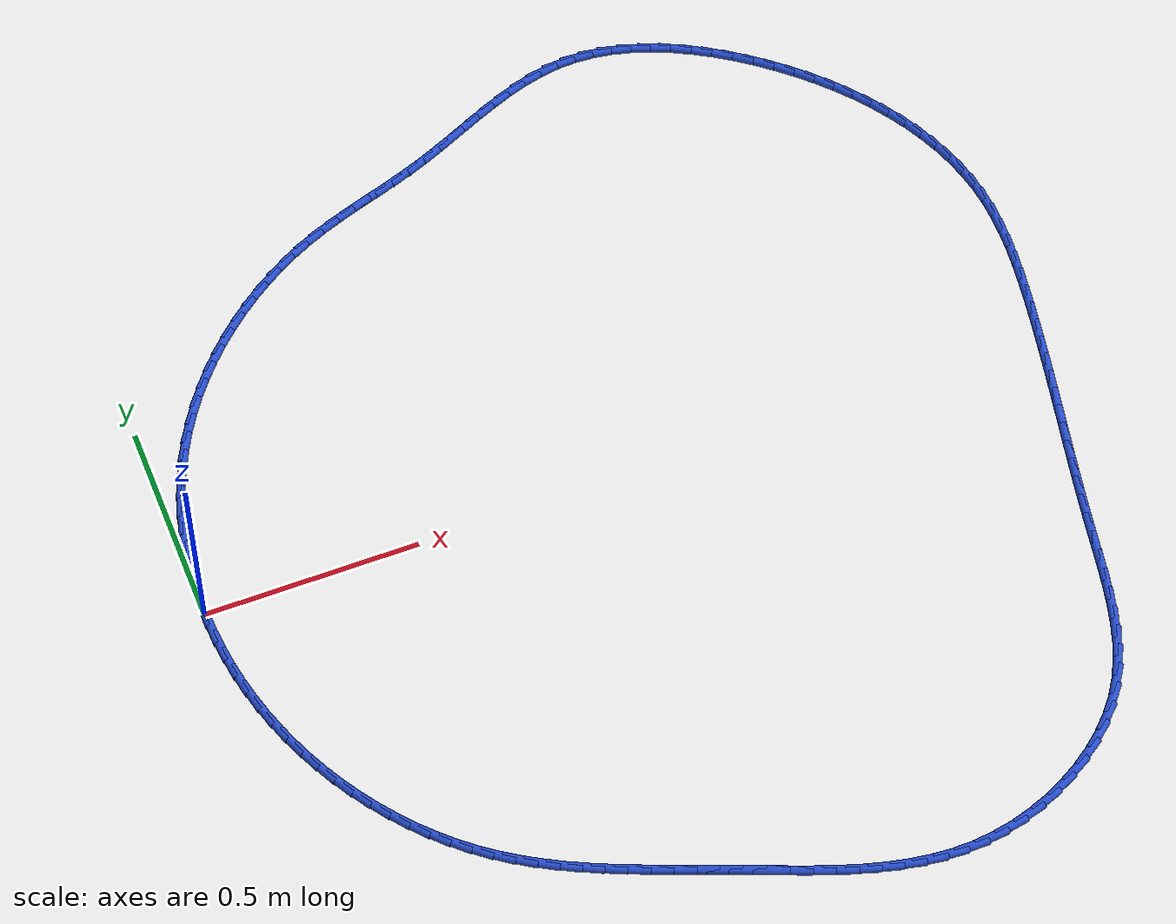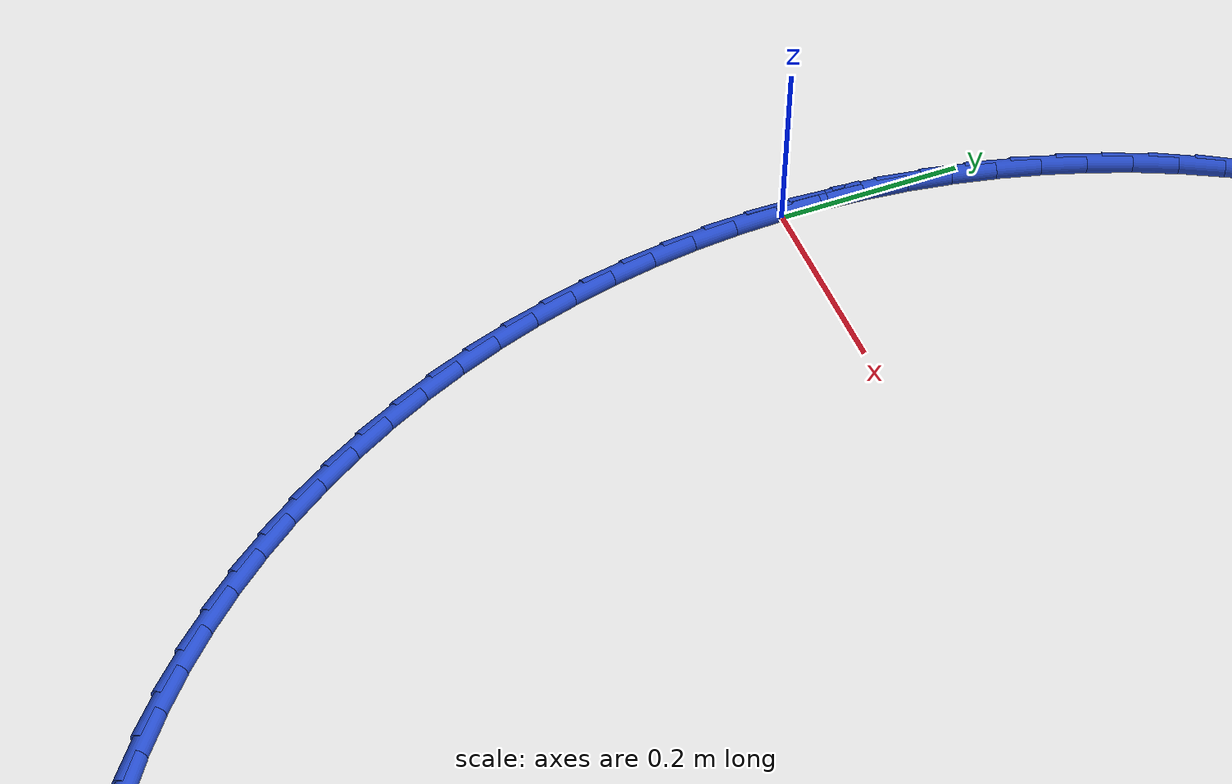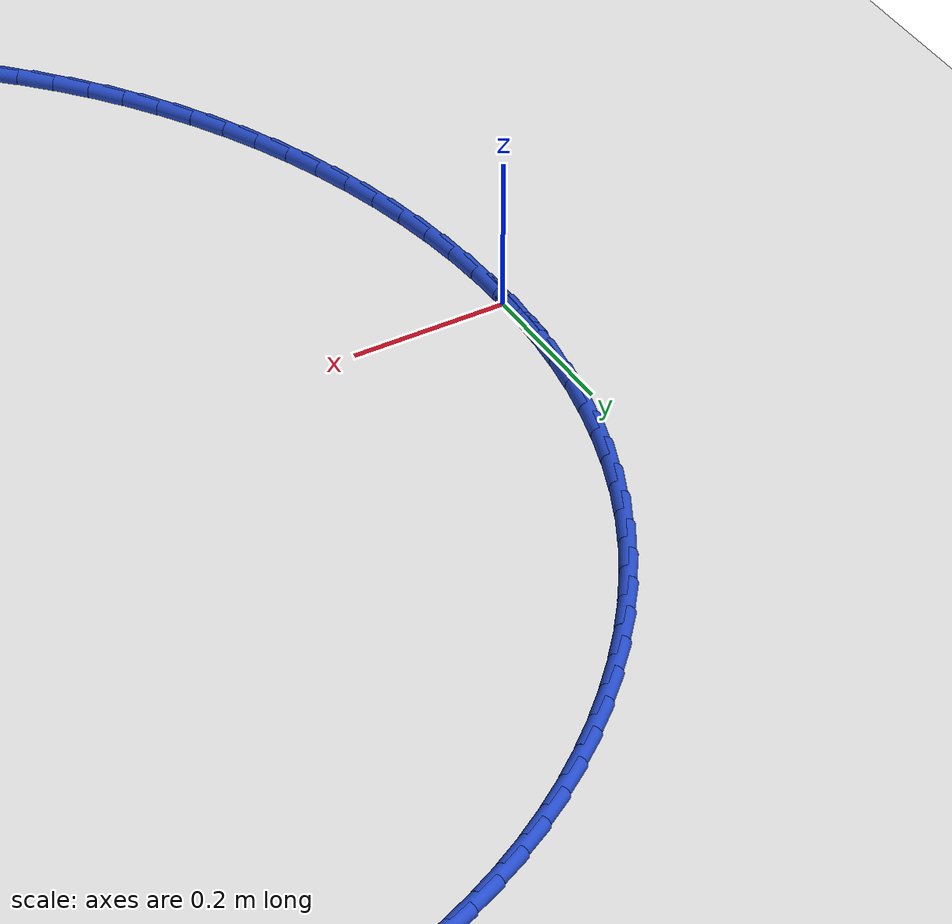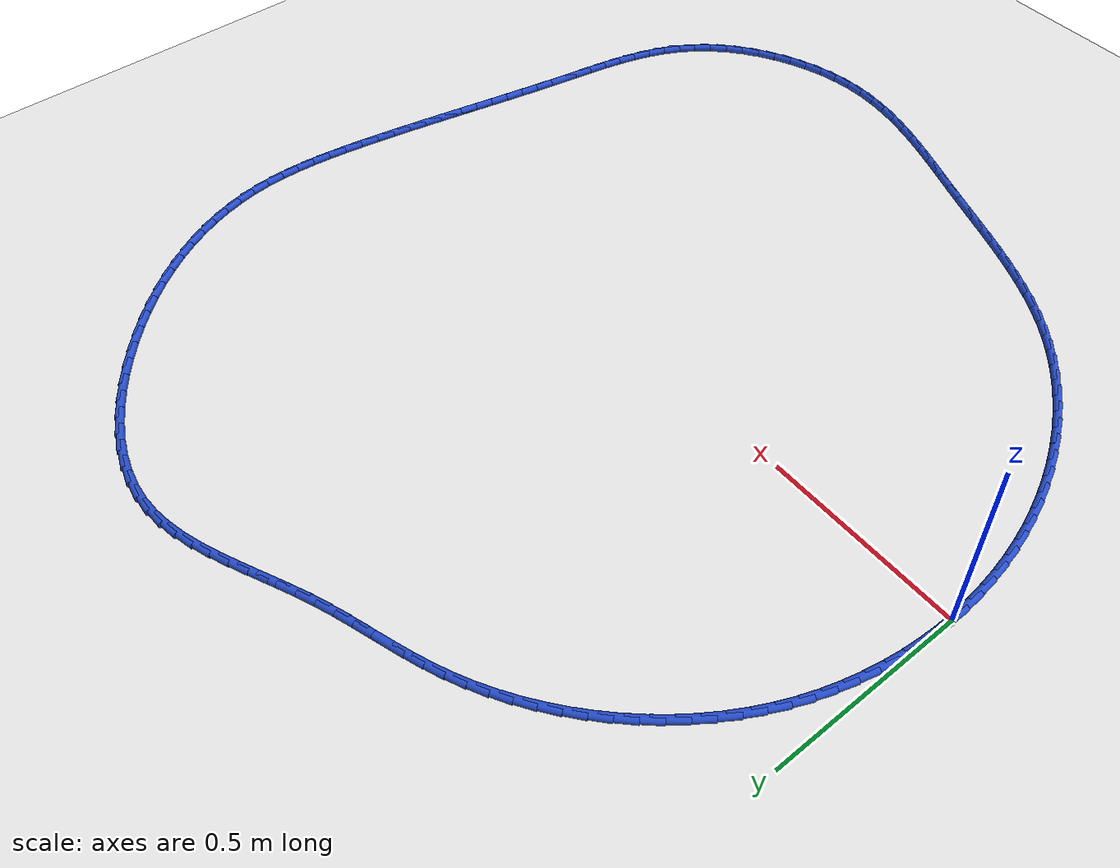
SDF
<sdf version="1.6">
 <world name="default">
  <light name="sun" type="directional">
   <pose>0 0 10 0 -0 0</pose>
   <diffuse>0.8 0.8 0.8 1</diffuse>
   <specular>0.2 0.2 0.2 1</specular>
   <attenuation>
    <range>1000</range>
    <constant>0.9</constant>
    <linear>0.01</linear>
    <quadratic>0.001</quadratic>
   </attenuation>
   <direction>-0.5 0.1 -0.9</direction>
  </light>
  <model name="ground_plane">
   <static>1</static>
   <link name="link">
    <collision name="collision">
     <geometry><plane><normal>0 0 1</normal><size>100 100</size></plane></geometry>
     <surface><friction><ode><mu>100</mu><mu2>50</mu2></ode></friction></surface>
    </collision>
    <visual name="visual">
     <cast_shadows>0</cast_shadows>
     <geometry><plane><normal>0 0 1</normal><size>100 100</size></plane></geometry>
     <material>
      <script><uri>file://media/materials/scripts/gazebo.material</uri><name>Gazebo/WhiteGlow</name></script>
     </material>
    </visual>
   </link>
  </model>
  <gravity>0 0 -9.8</gravity>
  <magnetic_field>6e-06 2.3e-05 -4.2e-05</magnetic_field>
  <atmosphere type="adiabatic"/>
  <physics name="default_physics" default="0" type="ode">
   <max_step_size>0.001</max_step_size>
   <real_time_factor>1</real_time_factor>
   <real_time_update_rate>1000</real_time_update_rate>
  </physics>
  <scene><ambient>0.4 0.4 0.4 1</ambient><background>0.7 0.7 0.7 1</background><shadows>1</shadows></scene>
  <spherical_coordinates>
   <surface_model>EARTH_WGS84</surface_model>
   <latitude_deg>0</latitude_deg>
   <longitude_deg>0</longitude_deg>
   <elevation>0</elevation>
   <heading_deg>0</heading_deg>
  </spherical_coordinates>
  <model name="line">
   <link name="link_0">
    <pose>-3.469446951953614e-17 2.7755575615628914e-17 0.01 0 1.57 1.5528366445297883</pose>
    <collision name="collision">
     <geometry><cylinder><radius>0.01</radius><length>0.08</length></cylinder></geometry>
    </collision>
    <visual name="visual">
     <material>
      <script><name>Gazebo/Blue</name><uri>file://media/materials/scripts/gazebo.material</uri></script>
     </material>
     <geometry><cylinder><radius>0.01</radius><length>0.08</length></cylinder></geometry>
    </visual>
   </link>
   <link name="link_1">
    <pose>0.0008686224491461033 0.04835993437259867 0.01 0 1.57 1.5050240430879447</pose>
    <collision name="collision">
     <geometry><cylinder><radius>0.01</radius><length>0.08</length></cylinder></geometry>
    </collision>
    <visual name="visual">
     <material>
      <script><name>Gazebo/Blue</name><uri>file://media/materials/scripts/gazebo.material</uri></script>
     </material>
     <geometry><cylinder><radius>0.01</radius><length>0.08</length></cylinder></geometry>
    </visual>
   </link>
   <link name="link_2">
    <pose>0.004049572230710496 0.09665324816142548 0.01 0 1.57 1.4565509163530381</pose>
    <collision name="collision">
     <geometry><cylinder><radius>0.01</radius><length>0.08</length></cylinder></geometry>
    </collision>
    <visual name="visual">
     <material>
      <script><name>Gazebo/Blue</name><uri>file://media/materials/scripts/gazebo.material</uri></script>
     </material>
     <geometry><cylinder><radius>0.01</radius><length>0.08</length></cylinder></geometry>
    </visual>
   </link>
   <link name="link_3">
    <pose>0.009568877203612948 0.14475383574577572 0.01 0 1.57 1.4072758542930082</pose>
    <collision name="collision">
     <geometry><cylinder><radius>0.01</radius><length>0.08</length></cylinder></geometry>
    </collision>
    <visual name="visual">
     <material>
      <script><name>Gazebo/Blue</name><uri>file://media/materials/scripts/gazebo.material</uri></script>
     </material>
     <geometry><cylinder><radius>0.01</radius><length>0.08</length></cylinder></geometry>
    </visual>
   </link>
   <link name="link_4">
    <pose>0.01745256522677327 0.19253559150494473 0.01 0 1.57 1.3570687809733968</pose>
    <collision name="collision">
     <geometry><cylinder><radius>0.01</radius><length>0.08</length></cylinder></geometry>
    </collision>
    <visual name="visual">
     <material>
      <script><name>Gazebo/Blue</name><uri>file://media/materials/scripts/gazebo.material</uri></script>
     </material>
     <geometry><cylinder><radius>0.01</radius><length>0.08</length></cylinder></geometry>
    </visual>
   </link>
   <link name="link_5">
    <pose>0.027726664159111285 0.23987240981822772 0.01 0 1.57 1.3058138103631676</pose>
    <collision name="collision">
     <geometry><cylinder><radius>0.01</radius><length>0.08</length></cylinder></geometry>
    </collision>
    <visual name="visual">
     <material>
      <script><name>Gazebo/Blue</name><uri>file://media/materials/scripts/gazebo.material</uri></script>
     </material>
     <geometry><cylinder><radius>0.01</radius><length>0.08</length></cylinder></geometry>
    </visual>
   </link>
   <link name="link_6">
    <pose>0.04041720185954682 0.28663818506492006 0.01 0 1.57 1.253412631626333</pose>
    <collision name="collision">
     <geometry><cylinder><radius>0.01</radius><length>0.08</length></cylinder></geometry>
    </collision>
    <visual name="visual">
     <material>
      <script><name>Gazebo/Blue</name><uri>file://media/materials/scripts/gazebo.material</uri></script>
     </material>
     <geometry><cylinder><radius>0.01</radius><length>0.08</length></cylinder></geometry>
    </visual>
   </link>
   <link name="link_7">
    <pose>0.05555020618699967 0.332706811624317 0.01 0 1.57 1.199788389402016</pose>
    <collision name="collision">
     <geometry><cylinder><radius>0.01</radius><length>0.08</length></cylinder></geometry>
    </collision>
    <visual name="visual">
     <material>
      <script><name>Gazebo/Blue</name><uri>file://media/materials/scripts/gazebo.material</uri></script>
     </material>
     <geometry><cylinder><radius>0.01</radius><length>0.08</length></cylinder></geometry>
    </visual>
   </link>
   <link name="link_8">
    <pose>0.07315170500038967 0.3779521838757138 0.01 0 1.57 1.1448899544182236</pose>
    <collision name="collision">
     <geometry><cylinder><radius>0.01</radius><length>0.08</length></cylinder></geometry>
    </collision>
    <visual name="visual">
     <material>
      <script><name>Gazebo/Blue</name><uri>file://media/materials/scripts/gazebo.material</uri></script>
     </material>
     <geometry><cylinder><radius>0.01</radius><length>0.08</length></cylinder></geometry>
    </visual>
   </link>
   <link name="link_9">
    <pose>0.09324772615863663 0.4222481961984057 0.01 0 1.57 1.088897441915029</pose>
    <collision name="collision">
     <geometry><cylinder><radius>0.01</radius><length>0.08</length></cylinder></geometry>
    </collision>
    <visual name="visual">
     <material>
      <script><name>Gazebo/Blue</name><uri>file://media/materials/scripts/gazebo.material</uri></script>
     </material>
     <geometry><cylinder><radius>0.01</radius><length>0.08</length></cylinder></geometry>
    </visual>
   </link>
   <link name="link_10">
    <pose>0.11585381420771197 0.46546986029225823 0.01 0 1.57 1.033608255612884</pose>
    <collision name="collision">
     <geometry><cylinder><radius>0.01</radius><length>0.08</length></cylinder></geometry>
    </collision>
    <visual name="visual">
     <material>
      <script><name>Gazebo/Blue</name><uri>file://media/materials/scripts/gazebo.material</uri></script>
     </material>
     <geometry><cylinder><radius>0.01</radius><length>0.08</length></cylinder></geometry>
    </visual>
   </link>
   <link name="link_11">
    <pose>0.14088901590209327 0.5075024726752998 0.01 0 1.57 0.9798238435687318</pose>
    <collision name="collision">
     <geometry><cylinder><radius>0.01</radius><length>0.08</length></cylinder></geometry>
    </collision>
    <visual name="visual">
     <material>
      <script><name>Gazebo/Blue</name><uri>file://media/materials/scripts/gazebo.material</uri></script>
     </material>
     <geometry><cylinder><radius>0.01</radius><length>0.08</length></cylinder></geometry>
    </visual>
   </link>
   <link name="link_12">
    <pose>0.16822037318388858 0.5482368725834857 0.01 0 1.57 0.9273157152720111</pose>
    <collision name="collision">
     <geometry><cylinder><radius>0.01</radius><length>0.08</length></cylinder></geometry>
    </collision>
    <visual name="visual">
     <material>
      <script><name>Gazebo/Blue</name><uri>file://media/materials/scripts/gazebo.material</uri></script>
     </material>
     <geometry><cylinder><radius>0.01</radius><length>0.08</length></cylinder></geometry>
    </visual>
   </link>
   <link name="link_13">
    <pose>0.19771442396720645 0.5875639529725115 0.01 0 1.57 0.8758332691027544</pose>
    <collision name="collision">
     <geometry><cylinder><radius>0.01</radius><length>0.08</length></cylinder></geometry>
    </collision>
    <visual name="visual">
     <material>
      <script><name>Gazebo/Blue</name><uri>file://media/materials/scripts/gazebo.material</uri></script>
     </material>
     <geometry><cylinder><radius>0.01</radius><length>0.08</length></cylinder></geometry>
    </visual>
   </link>
   <link name="link_14">
    <pose>0.22923770616615557 0.625374606798073 0.01 0 1.57 0.8251172474438313</pose>
    <collision name="collision">
     <geometry><cylinder><radius>0.01</radius><length>0.08</length></cylinder></geometry>
    </collision>
    <visual name="visual">
     <material>
      <script><name>Gazebo/Blue</name><uri>file://media/materials/scripts/gazebo.material</uri></script>
     </material>
     <geometry><cylinder><radius>0.01</radius><length>0.08</length></cylinder></geometry>
    </visual>
   </link>
   <link name="link_15">
    <pose>0.2626567576948446 0.6615597270158661 0.01 0 1.57 0.7749022123359494</pose>
    <collision name="collision">
     <geometry><cylinder><radius>0.01</radius><length>0.08</length></cylinder></geometry>
    </collision>
    <visual name="visual">
     <material>
      <script><name>Gazebo/Blue</name><uri>file://media/materials/scripts/gazebo.material</uri></script>
     </material>
     <geometry><cylinder><radius>0.01</radius><length>0.08</length></cylinder></geometry>
    </visual>
   </link>
   <link name="link_16">
    <pose>0.29783811646738223 0.6960102065815862 0.01 0 1.57 0.7249180292080372</pose>
    <collision name="collision">
     <geometry><cylinder><radius>0.01</radius><length>0.08</length></cylinder></geometry>
    </collision>
    <visual name="visual">
     <material>
      <script><name>Gazebo/Blue</name><uri>file://media/materials/scripts/gazebo.material</uri></script>
     </material>
     <geometry><cylinder><radius>0.01</radius><length>0.08</length></cylinder></geometry>
    </visual>
   </link>
   <link name="link_17">
    <pose>0.33464832039787706 0.7286169384509293 0.01 0 1.57 0.6748906751996312</pose>
    <collision name="collision">
     <geometry><cylinder><radius>0.01</radius><length>0.08</length></cylinder></geometry>
    </collision>
    <visual name="visual">
     <material>
      <script><name>Gazebo/Blue</name><uri>file://media/materials/scripts/gazebo.material</uri></script>
     </material>
     <geometry><cylinder><radius>0.01</radius><length>0.08</length></cylinder></geometry>
    </visual>
   </link>
   <link name="link_18">
    <pose>0.37295390740043777 0.7592708155795912 0.01 0 1.57 0.6245426824054108</pose>
    <collision name="collision">
     <geometry><cylinder><radius>0.01</radius><length>0.08</length></cylinder></geometry>
    </collision>
    <visual name="visual">
     <material>
      <script><name>Gazebo/Blue</name><uri>file://media/materials/scripts/gazebo.material</uri></script>
     </material>
     <geometry><cylinder><radius>0.01</radius><length>0.08</length></cylinder></geometry>
    </visual>
   </link>
   <link name="link_19">
    <pose>0.4126214153891729 0.7878627309232674 0.01 0 1.57 0.5735935279778767</pose>
    <collision name="collision">
     <geometry><cylinder><radius>0.01</radius><length>0.08</length></cylinder></geometry>
    </collision>
    <visual name="visual">
     <material>
      <script><name>Gazebo/Blue</name><uri>file://media/materials/scripts/gazebo.material</uri></script>
     </material>
     <geometry><cylinder><radius>0.01</radius><length>0.08</length></cylinder></geometry>
    </visual>
   </link>
   <link name="link_20">
    <pose>0.4535173822781913 0.814283577437654 0.01 0 1.57 0.5217602982170383</pose>
    <collision name="collision">
     <geometry><cylinder><radius>0.01</radius><length>0.08</length></cylinder></geometry>
    </collision>
    <visual name="visual">
     <material>
      <script><name>Gazebo/Blue</name><uri>file://media/materials/scripts/gazebo.material</uri></script>
     </material>
     <geometry><cylinder><radius>0.01</radius><length>0.08</length></cylinder></geometry>
    </visual>
   </link>
   <link name="link_21">
    <pose>0.49550834598160154 0.8384242480784464 0.01 0 1.57 0.4687589846407496</pose>
    <collision name="collision">
     <geometry><cylinder><radius>0.01</radius><length>0.08</length></cylinder></geometry>
    </collision>
    <visual name="visual">
     <material>
      <script><name>Gazebo/Blue</name><uri>file://media/materials/scripts/gazebo.material</uri></script>
     </material>
     <geometry><cylinder><radius>0.01</radius><length>0.08</length></cylinder></geometry>
    </visual>
   </link>
   <link name="link_22">
    <pose>0.5384608444135123 0.8601756358013407 0.01 0 1.57 0.4153699854165763</pose>
    <collision name="collision">
     <geometry><cylinder><radius>0.01</radius><length>0.08</length></cylinder></geometry>
    </collision>
    <visual name="visual">
     <material>
      <script><name>Gazebo/Blue</name><uri>file://media/materials/scripts/gazebo.material</uri></script>
     </material>
     <geometry><cylinder><radius>0.01</radius><length>0.08</length></cylinder></geometry>
    </visual>
   </link>
   <link name="link_23">
    <pose>0.5822396941860251 0.8794834482159868 0.01 0 1.57 0.3711278010609873</pose>
    <collision name="collision">
     <geometry><cylinder><radius>0.01</radius><length>0.08</length></cylinder></geometry>
    </collision>
    <visual name="visual">
     <material>
      <script><name>Gazebo/Blue</name><uri>file://media/materials/scripts/gazebo.material</uri></script>
     </material>
     <geometry><cylinder><radius>0.01</radius><length>0.08</length></cylinder></geometry>
    </visual>
   </link>
   <link name="link_24">
    <pose>0.6266943225736682 0.8967834645233083 0.01 0 1.57 0.34153641652506805</pose>
    <collision name="collision">
     <geometry><cylinder><radius>0.01</radius><length>0.08</length></cylinder></geometry>
    </collision>
    <visual name="visual">
     <material>
      <script><name>Gazebo/Blue</name><uri>file://media/materials/scripts/gazebo.material</uri></script>
     </material>
     <geometry><cylinder><radius>0.01</radius><length>0.08</length></cylinder></geometry>
    </visual>
   </link>
   <link name="link_25">
    <pose>0.6716660568045066 0.9127694089228885 0.01 0 1.57 0.32686163205670815</pose>
    <collision name="collision">
     <geometry><cylinder><radius>0.01</radius><length>0.08</length></cylinder></geometry>
    </collision>
    <visual name="visual">
     <material>
      <script><name>Gazebo/Blue</name><uri>file://media/materials/scripts/gazebo.material</uri></script>
     </material>
     <geometry><cylinder><radius>0.01</radius><length>0.08</length></cylinder></geometry>
    </visual>
   </link>
   <link name="link_26">
    <pose>0.7169961517241952 0.9281373106234055 0.01 0 1.57 0.3270647680079634</pose>
    <collision name="collision">
     <geometry><cylinder><radius>0.01</radius><length>0.08</length></cylinder></geometry>
    </collision>
    <visual name="visual">
     <material>
      <script><name>Gazebo/Blue</name><uri>file://media/materials/scripts/gazebo.material</uri></script>
     </material>
     <geometry><cylinder><radius>0.01</radius><length>0.08</length></cylinder></geometry>
    </visual>
   </link>
   <link name="link_27">
    <pose>0.7625258621783879 0.9435831988335366 0.01 0 1.57 0.34194723040738334</pose>
    <collision name="collision">
     <geometry><cylinder><radius>0.01</radius><length>0.08</length></cylinder></geometry>
    </collision>
    <visual name="visual">
     <material>
      <script><name>Gazebo/Blue</name><uri>file://media/materials/scripts/gazebo.material</uri></script>
     </material>
     <geometry><cylinder><radius>0.01</radius><length>0.08</length></cylinder></geometry>
    </visual>
   </link>
   <link name="link_28">
    <pose>0.8080964430127398 0.95980310276196 0.01 0 1.57 0.3711517643739013</pose>
    <collision name="collision">
     <geometry><cylinder><radius>0.01</radius><length>0.08</length></cylinder></geometry>
    </collision>
    <visual name="visual">
     <material>
      <script><name>Gazebo/Blue</name><uri>file://media/materials/scripts/gazebo.material</uri></script>
     </material>
     <geometry><cylinder><radius>0.01</radius><length>0.08</length></cylinder></geometry>
    </visual>
   </link>
   <link name="link_29">
    <pose>0.8535491869157628 0.9774928010612357 0.01 0 1.57 0.4076074209221799</pose>
    <collision name="collision">
     <geometry><cylinder><radius>0.01</radius><length>0.08</length></cylinder></geometry>
    </collision>
    <visual name="visual">
     <material>
      <script><name>Gazebo/Blue</name><uri>file://media/materials/scripts/gazebo.material</uri></script>
     </material>
     <geometry><cylinder><radius>0.01</radius><length>0.08</length></cylinder></geometry>
    </visual>
   </link>
   <link name="link_30">
    <pose>0.898774822295596 0.997020760370592 0.01 0 1.57 0.4320042545859119</pose>
    <collision name="collision">
     <geometry><cylinder><radius>0.01</radius><length>0.08</length></cylinder></geometry>
    </collision>
    <visual name="visual">
     <material>
      <script><name>Gazebo/Blue</name><uri>file://media/materials/scripts/gazebo.material</uri></script>
     </material>
     <geometry><cylinder><radius>0.01</radius><length>0.08</length></cylinder></geometry>
    </visual>
   </link>
   <link name="link_31">
    <pose>0.9438107219773708 1.0177845202398654 0.01 0 1.57 0.4413637397500417</pose>
    <collision name="collision">
     <geometry><cylinder><radius>0.01</radius><length>0.08</length></cylinder></geometry>
    </collision>
    <visual name="visual">
     <material>
      <script><name>Gazebo/Blue</name><uri>file://media/materials/scripts/gazebo.material</uri></script>
     </material>
     <geometry><cylinder><radius>0.01</radius><length>0.08</length></cylinder></geometry>
    </visual>
   </link>
   <link name="link_32">
    <pose>0.9887213235131233 1.0390024256947603 0.01 0 1.57 0.43590400869756685</pose>
    <collision name="collision">
     <geometry><cylinder><radius>0.01</radius><length>0.08</length></cylinder></geometry>
    </collision>
    <visual name="visual">
     <material>
      <script><name>Gazebo/Blue</name><uri>file://media/materials/scripts/gazebo.material</uri></script>
     </material>
     <geometry><cylinder><radius>0.01</radius><length>0.08</length></cylinder></geometry>
    </visual>
   </link>
   <link name="link_33">
    <pose>1.0335710644548894 1.0598928217609822 0.01 0 1.57 0.4153615110476163</pose>
    <collision name="collision">
     <geometry><cylinder><radius>0.01</radius><length>0.08</length></cylinder></geometry>
    </collision>
    <visual name="visual">
     <material>
      <script><name>Gazebo/Blue</name><uri>file://media/materials/scripts/gazebo.material</uri></script>
     </material>
     <geometry><cylinder><radius>0.01</radius><length>0.08</length></cylinder></geometry>
    </visual>
   </link>
   <link name="link_34">
    <pose>1.0784243823547055 1.0796740534642344 0.01 0 1.57 0.3790062946709613</pose>
    <collision name="collision">
     <geometry><cylinder><radius>0.01</radius><length>0.08</length></cylinder></geometry>
    </collision>
    <visual name="visual">
     <material>
      <script><name>Gazebo/Blue</name><uri>file://media/materials/scripts/gazebo.material</uri></script>
     </material>
     <geometry><cylinder><radius>0.01</radius><length>0.08</length></cylinder></geometry>
    </visual>
   </link>
   <link name="link_35">
    <pose>1.123345714764607 1.0975644658302217 0.01 0 1.57 0.32574064173560174</pose>
    <collision name="collision">
     <geometry><cylinder><radius>0.01</radius><length>0.08</length></cylinder></geometry>
    </collision>
    <visual name="visual">
     <material>
      <script><name>Gazebo/Blue</name><uri>file://media/materials/scripts/gazebo.material</uri></script>
     </material>
     <geometry><cylinder><radius>0.01</radius><length>0.08</length></cylinder></geometry>
    </visual>
   </link>
   <link name="link_36">
    <pose>1.1683994992366311 1.1127824038846492 0.01 0 1.57 0.254339772181018</pose>
    <collision name="collision">
     <geometry><cylinder><radius>0.01</radius><length>0.08</length></cylinder></geometry>
    </collision>
    <visual name="visual">
     <material>
      <script><name>Gazebo/Blue</name><uri>file://media/materials/scripts/gazebo.material</uri></script>
     </material>
     <geometry><cylinder><radius>0.01</radius><length>0.08</length></cylinder></geometry>
    </visual>
   </link>
   <link name="link_37">
    <pose>1.213650173322814 1.1245462126532215 0.01 0 1.57 0.16392325335727587</pose>
    <collision name="collision">
     <geometry><cylinder><radius>0.01</radius><length>0.08</length></cylinder></geometry>
    </collision>
    <visual name="visual">
     <material>
      <script><name>Gazebo/Blue</name><uri>file://media/materials/scripts/gazebo.material</uri></script>
     </material>
     <geometry><cylinder><radius>0.01</radius><length>0.08</length></cylinder></geometry>
    </visual>
   </link>
   <link name="link_38">
    <pose>1.2591621745751909 1.1320742371616423 0.01 0 1.57 0.05522889531277607</pose>
    <collision name="collision">
     <geometry><cylinder><radius>0.01</radius><length>0.08</length></cylinder></geometry>
    </collision>
    <visual name="visual">
     <material>
      <script><name>Gazebo/Blue</name><uri>file://media/materials/scripts/gazebo.material</uri></script>
     </material>
     <geometry><cylinder><radius>0.01</radius><length>0.08</length></cylinder></geometry>
    </visual>
   </link>
   <link name="link_39">
    <pose>1.3049946946627782 1.1346080934217175 0.01 0 1.57 -0.05784616686105402</pose>
    <collision name="collision">
     <geometry><cylinder><radius>0.01</radius><length>0.08</length></cylinder></geometry>
    </collision>
    <visual name="visual">
     <material>
      <script><name>Gazebo/Blue</name><uri>file://media/materials/scripts/gazebo.material</uri></script>
     </material>
     <geometry><cylinder><radius>0.01</radius><length>0.08</length></cylinder></geometry>
    </visual>
   </link>
   <link name="link_40">
    <pose>1.351083011830445 1.1319390832769252 0.01 0 1.57 -0.1615725403493236</pose>
    <collision name="collision">
     <geometry><cylinder><radius>0.01</radius><length>0.08</length></cylinder></geometry>
    </collision>
    <visual name="visual">
     <material>
      <script><name>Gazebo/Blue</name><uri>file://media/materials/scripts/gazebo.material</uri></script>
     </material>
     <geometry><cylinder><radius>0.01</radius><length>0.08</length></cylinder></geometry>
    </visual>
   </link>
   <link name="link_41">
    <pose>1.3972366533434708 1.1244163458855903 0.01 0 1.57 -0.25511027977849404</pose>
    <collision name="collision">
     <geometry><cylinder><radius>0.01</radius><length>0.08</length></cylinder></geometry>
    </collision>
    <visual name="visual">
     <material>
      <script><name>Gazebo/Blue</name><uri>file://media/materials/scripts/gazebo.material</uri></script>
     </material>
     <geometry><cylinder><radius>0.01</radius><length>0.08</length></cylinder></geometry>
    </visual>
   </link>
   <link name="link_42">
    <pose>1.4432595330480604 1.1124139217995193 0.01 0 1.57 -0.3389045160760979</pose>
    <collision name="collision">
     <geometry><cylinder><radius>0.01</radius><length>0.08</length></cylinder></geometry>
    </collision>
    <visual name="visual">
     <material>
      <script><name>Gazebo/Blue</name><uri>file://media/materials/scripts/gazebo.material</uri></script>
     </material>
     <geometry><cylinder><radius>0.01</radius><length>0.08</length></cylinder></geometry>
    </visual>
   </link>
   <link name="link_43">
    <pose>1.4889555647904191 1.096305851570519 0.01 0 1.57 -0.4138299654865193</pose>
    <collision name="collision">
     <geometry><cylinder><radius>0.01</radius><length>0.08</length></cylinder></geometry>
    </collision>
    <visual name="visual">
     <material>
      <script><name>Gazebo/Blue</name><uri>file://media/materials/scripts/gazebo.material</uri></script>
     </material>
     <geometry><cylinder><radius>0.01</radius><length>0.08</length></cylinder></geometry>
    </visual>
   </link>
   <link name="link_44">
    <pose>1.534128662416753 1.0764661757503957 0.01 0 1.57 -0.48095463164843427</pose>
    <collision name="collision">
     <geometry><cylinder><radius>0.01</radius><length>0.08</length></cylinder></geometry>
    </collision>
    <visual name="visual">
     <material>
      <script><name>Gazebo/Blue</name><uri>file://media/materials/scripts/gazebo.material</uri></script>
     </material>
     <geometry><cylinder><radius>0.01</radius><length>0.08</length></cylinder></geometry>
    </visual>
   </link>
   <link name="link_45">
    <pose>1.5785827397732668 1.0532689348909567 0.01 0 1.57 -0.5413880278359187</pose>
    <collision name="collision">
     <geometry><cylinder><radius>0.01</radius><length>0.08</length></cylinder></geometry>
    </collision>
    <visual name="visual">
     <material>
      <script><name>Gazebo/Blue</name><uri>file://media/materials/scripts/gazebo.material</uri></script>
     </material>
     <geometry><cylinder><radius>0.01</radius><length>0.08</length></cylinder></geometry>
    </visual>
   </link>
   <link name="link_46">
    <pose>1.6221217107061665 1.0270881695440075 0.01 0 1.57 -0.5961986751052533</pose>
    <collision name="collision">
     <geometry><cylinder><radius>0.01</radius><length>0.08</length></cylinder></geometry>
    </collision>
    <visual name="visual">
     <material>
      <script><name>Gazebo/Blue</name><uri>file://media/materials/scripts/gazebo.material</uri></script>
     </material>
     <geometry><cylinder><radius>0.01</radius><length>0.08</length></cylinder></geometry>
    </visual>
   </link>
   <link name="link_47">
    <pose>1.664549489061656 0.9982979202613551 0.01 0 1.57 -0.6463791659625971</pose>
    <collision name="collision">
     <geometry><cylinder><radius>0.01</radius><length>0.08</length></cylinder></geometry>
    </collision>
    <visual name="visual">
     <material>
      <script><name>Gazebo/Blue</name><uri>file://media/materials/scripts/gazebo.material</uri></script>
     </material>
     <geometry><cylinder><radius>0.01</radius><length>0.08</length></cylinder></geometry>
    </visual>
   </link>
   <link name="link_48">
    <pose>1.7056699886859419 0.967272227594806 0.01 0 1.57 -0.6928458052720089</pose>
    <collision name="collision">
     <geometry><cylinder><radius>0.01</radius><length>0.08</length></cylinder></geometry>
    </collision>
    <visual name="visual">
     <material>
      <script><name>Gazebo/Blue</name><uri>file://media/materials/scripts/gazebo.material</uri></script>
     </material>
     <geometry><cylinder><radius>0.01</radius><length>0.08</length></cylinder></geometry>
    </visual>
   </link>
   <link name="link_49">
    <pose>1.7452871660929337 0.9343847530878402 0.01 0 1.57 -0.7375283353098322</pose>
    <collision name="collision">
     <geometry><cylinder><radius>0.01</radius><length>0.08</length></cylinder></geometry>
    </collision>
    <visual name="visual">
     <material>
      <script><name>Gazebo/Blue</name><uri>file://media/materials/scripts/gazebo.material</uri></script>
     </material>
     <geometry><cylinder><radius>0.01</radius><length>0.08</length></cylinder></geometry>
    </visual>
   </link>
   <link name="link_50">
    <pose>1.7832144196179895 0.8999252885533212 0.01 0 1.57 -0.7834337093915305</pose>
    <collision name="collision">
     <geometry><cylinder><radius>0.01</radius><length>0.08</length></cylinder></geometry>
    </collision>
    <visual name="visual">
     <material>
      <script><name>Gazebo/Blue</name><uri>file://media/materials/scripts/gazebo.material</uri></script>
     </material>
     <geometry><cylinder><radius>0.01</radius><length>0.08</length></cylinder></geometry>
    </visual>
   </link>
   <link name="link_51">
    <pose>1.8192864115579155 0.8639947424696024 0.01 0 1.57 -0.8312082228976029</pose>
    <collision name="collision">
     <geometry><cylinder><radius>0.01</radius><length>0.08</length></cylinder></geometry>
    </collision>
    <visual name="visual">
     <material>
      <script><name>Gazebo/Blue</name><uri>file://media/materials/scripts/gazebo.material</uri></script>
     </material>
     <geometry><cylinder><radius>0.01</radius><length>0.08</length></cylinder></geometry>
    </visual>
   </link>
   <link name="link_52">
    <pose>1.8533407123031875 0.8266681913255103 0.01 0 1.57 -0.8811501203486982</pose>
    <collision name="collision">
     <geometry><cylinder><radius>0.01</radius><length>0.08</length></cylinder></geometry>
    </collision>
    <visual name="visual">
     <material>
      <script><name>Gazebo/Blue</name><uri>file://media/materials/scripts/gazebo.material</uri></script>
     </material>
     <geometry><cylinder><radius>0.01</radius><length>0.08</length></cylinder></geometry>
    </visual>
   </link>
   <link name="link_53">
    <pose>1.8852148922442828 0.7880207116098722 0.01 0 1.57 -0.9335549116139343</pose>
    <collision name="collision">
     <geometry><cylinder><radius>0.01</radius><length>0.08</length></cylinder></geometry>
    </collision>
    <visual name="visual">
     <material>
      <script><name>Gazebo/Blue</name><uri>file://media/materials/scripts/gazebo.material</uri></script>
     </material>
     <geometry><cylinder><radius>0.01</radius><length>0.08</length></cylinder></geometry>
    </visual>
   </link>
   <link name="link_54">
    <pose>1.9147465217716784 0.7481273798115157 0.01 0 1.57 -0.9887078555300849</pose>
    <collision name="collision">
     <geometry><cylinder><radius>0.01</radius><length>0.08</length></cylinder></geometry>
    </collision>
    <visual name="visual">
     <material>
      <script><name>Gazebo/Blue</name><uri>file://media/materials/scripts/gazebo.material</uri></script>
     </material>
     <geometry><cylinder><radius>0.01</radius><length>0.08</length></cylinder></geometry>
    </visual>
   </link>
   <link name="link_55">
    <pose>1.941773171275851 0.7070632724192671 0.01 0 1.57 -1.04687270124007</pose>
    <collision name="collision">
     <geometry><cylinder><radius>0.01</radius><length>0.08</length></cylinder></geometry>
    </collision>
    <visual name="visual">
     <material>
      <script><name>Gazebo/Blue</name><uri>file://media/materials/scripts/gazebo.material</uri></script>
     </material>
     <geometry><cylinder><radius>0.01</radius><length>0.08</length></cylinder></geometry>
    </visual>
   </link>
   <link name="link_56">
    <pose>1.9661324111472758 0.6649034659219539 0.01 0 1.57 -1.1082760466651738</pose>
    <collision name="collision">
     <geometry><cylinder><radius>0.01</radius><length>0.08</length></cylinder></geometry>
    </collision>
    <visual name="visual">
     <material>
      <script><name>Gazebo/Blue</name><uri>file://media/materials/scripts/gazebo.material</uri></script>
     </material>
     <geometry><cylinder><radius>0.01</radius><length>0.08</length></cylinder></geometry>
    </visual>
   </link>
   <link name="link_57">
    <pose>1.9876618117764304 0.6217230368084029 0.01 0 1.57 -1.173087001263785</pose>
    <collision name="collision">
     <geometry><cylinder><radius>0.01</radius><length>0.08</length></cylinder></geometry>
    </collision>
    <visual name="visual">
     <material>
      <script><name>Gazebo/Blue</name><uri>file://media/materials/scripts/gazebo.material</uri></script>
     </material>
     <geometry><cylinder><radius>0.01</radius><length>0.08</length></cylinder></geometry>
    </visual>
   </link>
   <link name="link_58">
    <pose>2.006198943553792 0.5775970615674416 0.01 0 1.57 -1.2413925232892395</pose>
    <collision name="collision">
     <geometry><cylinder><radius>0.01</radius><length>0.08</length></cylinder></geometry>
    </collision>
    <visual name="visual">
     <material>
      <script><name>Gazebo/Blue</name><uri>file://media/materials/scripts/gazebo.material</uri></script>
     </material>
     <geometry><cylinder><radius>0.01</radius><length>0.08</length></cylinder></geometry>
    </visual>
   </link>
   <link name="link_59">
    <pose>2.021581376869836 0.5326006166878965 0.01 0 1.57 -1.3131699268003998</pose>
    <collision name="collision">
     <geometry><cylinder><radius>0.01</radius><length>0.08</length></cylinder></geometry>
    </collision>
    <visual name="visual">
     <material>
      <script><name>Gazebo/Blue</name><uri>file://media/materials/scripts/gazebo.material</uri></script>
     </material>
     <geometry><cylinder><radius>0.01</radius><length>0.08</length></cylinder></geometry>
    </visual>
   </link>
   <link name="link_60">
    <pose>2.033646682115039 0.48680877865859534 0.01 0 1.57 -1.3882595885692735</pose>
    <collision name="collision">
     <geometry><cylinder><radius>0.01</radius><length>0.08</length></cylinder></geometry>
    </collision>
    <visual name="visual">
     <material>
      <script><name>Gazebo/Blue</name><uri>file://media/materials/scripts/gazebo.material</uri></script>
     </material>
     <geometry><cylinder><radius>0.01</radius><length>0.08</length></cylinder></geometry>
    </visual>
   </link>
   <link name="link_61">
    <pose>2.042232429679879 0.4402966239683646 0.01 0 1.57 -1.4645999882853815</pose>
    <collision name="collision">
     <geometry><cylinder><radius>0.01</radius><length>0.08</length></cylinder></geometry>
    </collision>
    <visual name="visual">
     <material>
      <script><name>Gazebo/Blue</name><uri>file://media/materials/scripts/gazebo.material</uri></script>
     </material>
     <geometry><cylinder><radius>0.01</radius><length>0.08</length></cylinder></geometry>
    </visual>
   </link>
   <link name="link_62">
    <pose>2.0472582891499553 0.3931485583670903 0.01 0 1.57 -1.5332784316409203</pose>
    <collision name="collision">
     <geometry><cylinder><radius>0.01</radius><length>0.08</length></cylinder></geometry>
    </collision>
    <visual name="visual">
     <material>
      <script><name>Gazebo/Blue</name><uri>file://media/materials/scripts/gazebo.material</uri></script>
     </material>
     <geometry><cylinder><radius>0.01</radius><length>0.08</length></cylinder></geometry>
    </visual>
   </link>
   <link name="link_63">
    <pose>2.049046997579802 0.34549478977891857 0.01 0 1.57 1.5499265720559114</pose>
    <collision name="collision">
     <geometry><cylinder><radius>0.01</radius><length>0.08</length></cylinder></geometry>
    </collision>
    <visual name="visual">
     <material>
      <script><name>Gazebo/Blue</name><uri>file://media/materials/scripts/gazebo.material</uri></script>
     </material>
     <geometry><cylinder><radius>0.01</radius><length>0.08</length></cylinder></geometry>
    </visual>
   </link>
   <link name="link_64">
    <pose>2.0480447859872455 0.2974795592427063 0.01 0 1.57 1.501516984656453</pose>
    <collision name="collision">
     <geometry><cylinder><radius>0.01</radius><length>0.08</length></cylinder></geometry>
    </collision>
    <visual name="visual">
     <material>
      <script><name>Gazebo/Blue</name><uri>file://media/materials/scripts/gazebo.material</uri></script>
     </material>
     <geometry><cylinder><radius>0.01</radius><length>0.08</length></cylinder></geometry>
    </visual>
   </link>
   <link name="link_65">
    <pose>2.0446979174458133 0.24924711143992687 0.01 0 1.57 1.4626347220218594</pose>
    <collision name="collision">
     <geometry><cylinder><radius>0.01</radius><length>0.08</length></cylinder></geometry>
    </collision>
    <visual name="visual">
     <material>
      <script><name>Gazebo/Blue</name><uri>file://media/materials/scripts/gazebo.material</uri></script>
     </material>
     <geometry><cylinder><radius>0.01</radius><length>0.08</length></cylinder></geometry>
    </visual>
   </link>
   <link name="link_66">
    <pose>2.0394526550290335 0.20094169105205373 0.01 0 1.57 1.432826793895521</pose>
    <collision name="collision">
     <geometry><cylinder><radius>0.01</radius><length>0.08</length></cylinder></geometry>
    </collision>
    <visual name="visual">
     <material>
      <script><name>Gazebo/Blue</name><uri>file://media/materials/scripts/gazebo.material</uri></script>
     </material>
     <geometry><cylinder><radius>0.01</radius><length>0.08</length></cylinder></geometry>
    </visual>
   </link>
   <link name="link_67">
    <pose>2.0327552618104328 0.15270754276056156 0.01 0 1.57 1.411729299558929</pose>
    <collision name="collision">
     <geometry><cylinder><radius>0.01</radius><length>0.08</length></cylinder></geometry>
    </collision>
    <visual name="visual">
     <material>
      <script><name>Gazebo/Blue</name><uri>file://media/materials/scripts/gazebo.material</uri></script>
     </material>
     <geometry><cylinder><radius>0.01</radius><length>0.08</length></cylinder></geometry>
    </visual>
   </link>
   <link name="link_68">
    <pose>2.025052000863539 0.10468891124692346 0.01 0 1.57 1.3984528297207297</pose>
    <collision name="collision">
     <geometry><cylinder><radius>0.01</radius><length>0.08</length></cylinder></geometry>
    </collision>
    <visual name="visual">
     <material>
      <script><name>Gazebo/Blue</name><uri>file://media/materials/scripts/gazebo.material</uri></script>
     </material>
     <geometry><cylinder><radius>0.01</radius><length>0.08</length></cylinder></geometry>
    </visual>
   </link>
   <link name="link_69">
    <pose>2.016752485740738 0.05700982512822193 0.01 0 1.57 1.3884985883237617</pose>
    <collision name="collision">
     <geometry><cylinder><radius>0.01</radius><length>0.08</length></cylinder></geometry>
    </collision>
    <visual name="visual">
     <material>
      <script><name>Gazebo/Blue</name><uri>file://media/materials/scripts/gazebo.material</uri></script>
     </material>
     <geometry><cylinder><radius>0.01</radius><length>0.08</length></cylinder></geometry>
    </visual>
   </link>
   <link name="link_70">
    <pose>2.008023923725216 0.009660600476475639 0.01 0 1.57 1.3801047005762934</pose>
    <collision name="collision">
     <geometry><cylinder><radius>0.01</radius><length>0.08</length></cylinder></geometry>
    </collision>
    <visual name="visual">
     <material>
      <script><name>Gazebo/Blue</name><uri>file://media/materials/scripts/gazebo.material</uri></script>
     </material>
     <geometry><cylinder><radius>0.01</radius><length>0.08</length></cylinder></geometry>
    </visual>
   </link>
   <link name="link_71">
    <pose>1.9989350898614466 -0.03742274236551915 0.01 0 1.57 1.3733126914370115</pose>
    <collision name="collision">
     <geometry><cylinder><radius>0.01</radius><length>0.08</length></cylinder></geometry>
    </collision>
    <visual name="visual">
     <material>
      <script><name>Gazebo/Blue</name><uri>file://media/materials/scripts/gazebo.material</uri></script>
     </material>
     <geometry><cylinder><radius>0.01</radius><length>0.08</length></cylinder></geometry>
    </visual>
   </link>
   <link name="link_72">
    <pose>1.9895544761353106 -0.08430433919154215 0.01 0 1.57 1.3681587415267245</pose>
    <collision name="collision">
     <geometry><cylinder><radius>0.01</radius><length>0.08</length></cylinder></geometry>
    </collision>
    <visual name="visual">
     <material>
      <script><name>Gazebo/Blue</name><uri>file://media/materials/scripts/gazebo.material</uri></script>
     </material>
     <geometry><cylinder><radius>0.01</radius><length>0.08</length></cylinder></geometry>
    </visual>
   </link>
   <link name="link_73">
    <pose>1.9799505745326915 -0.13104832579537357 0.01 0 1.57 1.3646684632932609</pose>
    <collision name="collision">
     <geometry><cylinder><radius>0.01</radius><length>0.08</length></cylinder></geometry>
    </collision>
    <visual name="visual">
     <material>
      <script><name>Gazebo/Blue</name><uri>file://media/materials/scripts/gazebo.material</uri></script>
     </material>
     <geometry><cylinder><radius>0.01</radius><length>0.08</length></cylinder></geometry>
    </visual>
   </link>
   <link name="link_74">
    <pose>1.9701918770394695 -0.17771883797079127 0.01 0 1.57 1.362856949237194</pose>
    <collision name="collision">
     <geometry><cylinder><radius>0.01</radius><length>0.08</length></cylinder></geometry>
    </collision>
    <visual name="visual">
     <material>
      <script><name>Gazebo/Blue</name><uri>file://media/materials/scripts/gazebo.material</uri></script>
     </material>
     <geometry><cylinder><radius>0.01</radius><length>0.08</length></cylinder></geometry>
    </visual>
   </link>
   <link name="link_75">
    <pose>1.9603468756415283 -0.22438001151157538 0.01 0 1.57 1.3627288609674097</pose>
    <collision name="collision">
     <geometry><cylinder><radius>0.01</radius><length>0.08</length></cylinder></geometry>
    </collision>
    <visual name="visual">
     <material>
      <script><name>Gazebo/Blue</name><uri>file://media/materials/scripts/gazebo.material</uri></script>
     </material>
     <geometry><cylinder><radius>0.01</radius><length>0.08</length></cylinder></geometry>
    </visual>
   </link>
   <link name="link_76">
    <pose>1.9504840623247492 -0.2710959822115053 0.01 0 1.57 1.3642785430743827</pose>
    <collision name="collision">
     <geometry><cylinder><radius>0.01</radius><length>0.08</length></cylinder></geometry>
    </collision>
    <visual name="visual">
     <material>
      <script><name>Gazebo/Blue</name><uri>file://media/materials/scripts/gazebo.material</uri></script>
     </material>
     <geometry><cylinder><radius>0.01</radius><length>0.08</length></cylinder></geometry>
    </visual>
   </link>
   <link name="link_77">
    <pose>1.940671929075014 -0.3179308858643604 0.01 0 1.57 1.3674901531322559</pose>
    <collision name="collision">
     <geometry><cylinder><radius>0.01</radius><length>0.08</length></cylinder></geometry>
    </collision>
    <visual name="visual">
     <material>
      <script><name>Gazebo/Blue</name><uri>file://media/materials/scripts/gazebo.material</uri></script>
     </material>
     <geometry><cylinder><radius>0.01</radius><length>0.08</length></cylinder></geometry>
    </visual>
   </link>
   <link name="link_78">
    <pose>1.9309789678782043 -0.36494885826392076 0.01 0 1.57 1.3723378067884895</pose>
    <collision name="collision">
     <geometry><cylinder><radius>0.01</radius><length>0.08</length></cylinder></geometry>
    </collision>
    <visual name="visual">
     <material>
      <script><name>Gazebo/Blue</name><uri>file://media/materials/scripts/gazebo.material</uri></script>
     </material>
     <geometry><cylinder><radius>0.01</radius><length>0.08</length></cylinder></geometry>
    </visual>
   </link>
   <link name="link_79">
    <pose>1.921473670720203 -0.4122140352039645 0.01 0 1.57 1.3787857442506184</pose>
    <collision name="collision">
     <geometry><cylinder><radius>0.01</radius><length>0.08</length></cylinder></geometry>
    </collision>
    <visual name="visual">
     <material>
      <script><name>Gazebo/Blue</name><uri>file://media/materials/scripts/gazebo.material</uri></script>
     </material>
     <geometry><cylinder><radius>0.01</radius><length>0.08</length></cylinder></geometry>
    </visual>
   </link>
   <link name="link_80">
    <pose>1.9122245295868914 -0.45979055247827144 0.01 0 1.57 1.3867885309609767</pose>
    <collision name="collision">
     <geometry><cylinder><radius>0.01</radius><length>0.08</length></cylinder></geometry>
    </collision>
    <visual name="visual">
     <material>
      <script><name>Gazebo/Blue</name><uri>file://media/materials/scripts/gazebo.material</uri></script>
     </material>
     <geometry><cylinder><radius>0.01</radius><length>0.08</length></cylinder></geometry>
    </visual>
   </link>
   <link name="link_81">
    <pose>1.903300036464152 -0.5077425458806211 0.01 0 1.57 1.3938473630042685</pose>
    <collision name="collision">
     <geometry><cylinder><radius>0.01</radius><length>0.08</length></cylinder></geometry>
    </collision>
    <visual name="visual">
     <material>
      <script><name>Gazebo/Blue</name><uri>file://media/materials/scripts/gazebo.material</uri></script>
     </material>
     <geometry><cylinder><radius>0.01</radius><length>0.08</length></cylinder></geometry>
    </visual>
   </link>
   <link name="link_82">
    <pose>1.8946588015698402 -0.556066410036178 0.01 0 1.57 1.3902241206906019</pose>
    <collision name="collision">
     <geometry><cylinder><radius>0.01</radius><length>0.08</length></cylinder></geometry>
    </collision>
    <visual name="visual">
     <material>
      <script><name>Gazebo/Blue</name><uri>file://media/materials/scripts/gazebo.material</uri></script>
     </material>
     <geometry><cylinder><radius>0.01</radius><length>0.08</length></cylinder></geometry>
    </visual>
   </link>
   <link name="link_83">
    <pose>1.8858190897737597 -0.604487070435527 0.01 0 1.57 1.3734938317183665</pose>
    <collision name="collision">
     <geometry><cylinder><radius>0.01</radius><length>0.08</length></cylinder></geometry>
    </collision>
    <visual name="visual">
     <material>
      <script><name>Gazebo/Blue</name><uri>file://media/materials/scripts/gazebo.material</uri></script>
     </material>
     <geometry><cylinder><radius>0.01</radius><length>0.08</length></cylinder></geometry>
    </visual>
   </link>
   <link name="link_84">
    <pose>1.8761888746590067 -0.6526614589358813 0.01 0 1.57 1.343367475687182</pose>
    <collision name="collision">
     <geometry><cylinder><radius>0.01</radius><length>0.08</length></cylinder></geometry>
    </collision>
    <visual name="visual">
     <material>
      <script><name>Gazebo/Blue</name><uri>file://media/materials/scripts/gazebo.material</uri></script>
     </material>
     <geometry><cylinder><radius>0.01</radius><length>0.08</length></cylinder></geometry>
    </visual>
   </link>
   <link name="link_85">
    <pose>1.8651761298086504 -0.7002465073944366 0.01 0 1.57 1.299287714988407</pose>
    <collision name="collision">
     <geometry><cylinder><radius>0.01</radius><length>0.08</length></cylinder></geometry>
    </collision>
    <visual name="visual">
     <material>
      <script><name>Gazebo/Blue</name><uri>file://media/materials/scripts/gazebo.material</uri></script>
     </material>
     <geometry><cylinder><radius>0.01</radius><length>0.08</length></cylinder></geometry>
    </visual>
   </link>
   <link name="link_86">
    <pose>1.8521888288057602 -0.7468991476683893 0.01 0 1.57 1.2405778758367656</pose>
    <collision name="collision">
     <geometry><cylinder><radius>0.01</radius><length>0.08</length></cylinder></geometry>
    </collision>
    <visual name="visual">
     <material>
      <script><name>Gazebo/Blue</name><uri>file://media/materials/scripts/gazebo.material</uri></script>
     </material>
     <geometry><cylinder><radius>0.01</radius><length>0.08</length></cylinder></geometry>
    </visual>
   </link>
   <link name="link_87">
    <pose>1.8366349452334056 -0.7922763116149356 0.01 0 1.57 1.166700270117607</pose>
    <collision name="collision">
     <geometry><cylinder><radius>0.01</radius><length>0.08</length></cylinder></geometry>
    </collision>
    <visual name="visual">
     <material>
      <script><name>Gazebo/Blue</name><uri>file://media/materials/scripts/gazebo.material</uri></script>
     </material>
     <geometry><cylinder><radius>0.01</radius><length>0.08</length></cylinder></geometry>
    </visual>
   </link>
   <link name="link_88">
    <pose>1.8179224526746567 -0.8360349310912701 0.01 0 1.57 1.077651963354923</pose>
    <collision name="collision">
     <geometry><cylinder><radius>0.01</radius><length>0.08</length></cylinder></geometry>
    </collision>
    <visual name="visual">
     <material>
      <script><name>Gazebo/Blue</name><uri>file://media/materials/scripts/gazebo.material</uri></script>
     </material>
     <geometry><cylinder><radius>0.01</radius><length>0.08</length></cylinder></geometry>
    </visual>
   </link>
   <link name="link_89">
    <pose>1.7954593247125825 -0.8778319379545897 0.01 0 1.57 0.9747529941736252</pose>
    <collision name="collision">
     <geometry><cylinder><radius>0.01</radius><length>0.08</length></cylinder></geometry>
    </collision>
    <visual name="visual">
     <material>
      <script><name>Gazebo/Blue</name><uri>file://media/materials/scripts/gazebo.material</uri></script>
     </material>
     <geometry><cylinder><radius>0.01</radius><length>0.08</length></cylinder></geometry>
    </visual>
   </link>
   <link name="link_90">
    <pose>1.768668636732932 -0.9173261944273331 0.01 0 1.57 0.8688655090806179</pose>
    <collision name="collision">
     <geometry><cylinder><radius>0.01</radius><length>0.08</length></cylinder></geometry>
    </collision>
    <visual name="visual">
     <material>
      <script><name>Gazebo/Blue</name><uri>file://media/materials/scripts/gazebo.material</uri></script>
     </material>
     <geometry><cylinder><radius>0.01</radius><length>0.08</length></cylinder></geometry>
    </visual>
   </link>
   <link name="link_91">
    <pose>1.7374560144334779 -0.9542382440007319 0.01 0 1.57 0.7704875501854702</pose>
    <collision name="collision">
     <geometry><cylinder><radius>0.01</radius><length>0.08</length></cylinder></geometry>
    </collision>
    <visual name="visual">
     <material>
      <script><name>Gazebo/Blue</name><uri>file://media/materials/scripts/gazebo.material</uri></script>
     </material>
     <geometry><cylinder><radius>0.01</radius><length>0.08</length></cylinder></geometry>
    </visual>
   </link>
   <link name="link_92">
    <pose>1.7022993879801922 -0.988361784125 0.01 0 1.57 0.6788575156633188</pose>
    <collision name="collision">
     <geometry><cylinder><radius>0.01</radius><length>0.08</length></cylinder></geometry>
    </collision>
    <visual name="visual">
     <material>
      <script><name>Gazebo/Blue</name><uri>file://media/materials/scripts/gazebo.material</uri></script>
     </material>
     <geometry><cylinder><radius>0.01</radius><length>0.08</length></cylinder></geometry>
    </visual>
   </link>
   <link name="link_93">
    <pose>1.6637099040803847 -1.0194947581048557 0.01 0 1.57 0.5924294088866922</pose>
    <collision name="collision">
     <geometry><cylinder><radius>0.01</radius><length>0.08</length></cylinder></geometry>
    </collision>
    <visual name="visual">
     <material>
      <script><name>Gazebo/Blue</name><uri>file://media/materials/scripts/gazebo.material</uri></script>
     </material>
     <geometry><cylinder><radius>0.01</radius><length>0.08</length></cylinder></geometry>
    </visual>
   </link>
   <link name="link_94">
    <pose>1.622198709441363 -1.0474351092450152 0.01 0 1.57 0.5096123799676534</pose>
    <collision name="collision">
     <geometry><cylinder><radius>0.01</radius><length>0.08</length></cylinder></geometry>
    </collision>
    <visual name="visual">
     <material>
      <script><name>Gazebo/Blue</name><uri>file://media/materials/scripts/gazebo.material</uri></script>
     </material>
     <geometry><cylinder><radius>0.01</radius><length>0.08</length></cylinder></geometry>
    </visual>
   </link>
   <link name="link_95">
    <pose>1.578276950770435 -1.0719807808501967 0.01 0 1.57 0.42881615281294577</pose>
    <collision name="collision">
     <geometry><cylinder><radius>0.01</radius><length>0.08</length></cylinder></geometry>
    </collision>
    <visual name="visual">
     <material>
      <script><name>Gazebo/Blue</name><uri>file://media/materials/scripts/gazebo.material</uri></script>
     </material>
     <geometry><cylinder><radius>0.01</radius><length>0.08</length></cylinder></geometry>
    </visual>
   </link>
   <link name="link_96">
    <pose>1.532455774774911 -1.0929297162251157 0.01 0 1.57 0.3484542522961835</pose>
    <collision name="collision">
     <geometry><cylinder><radius>0.01</radius><length>0.08</length></cylinder></geometry>
    </collision>
    <visual name="visual">
     <material>
      <script><name>Gazebo/Blue</name><uri>file://media/materials/scripts/gazebo.material</uri></script>
     </material>
     <geometry><cylinder><radius>0.01</radius><length>0.08</length></cylinder></geometry>
    </visual>
   </link>
   <link name="link_97">
    <pose>1.4852463281620991 -1.11007985867449 0.01 0 1.57 0.2669250072510236</pose>
    <collision name="collision">
     <geometry><cylinder><radius>0.01</radius><length>0.08</length></cylinder></geometry>
    </collision>
    <visual name="visual">
     <material>
      <script><name>Gazebo/Blue</name><uri>file://media/materials/scripts/gazebo.material</uri></script>
     </material>
     <geometry><cylinder><radius>0.01</radius><length>0.08</length></cylinder></geometry>
    </visual>
   </link>
   <link name="link_98">
    <pose>1.4371597576393076 -1.1232291515030361 0.01 0 1.57 0.1825858146033405</pose>
    <collision name="collision">
     <geometry><cylinder><radius>0.01</radius><length>0.08</length></cylinder></geometry>
    </collision>
    <visual name="visual">
     <material>
      <script><name>Gazebo/Blue</name><uri>file://media/materials/scripts/gazebo.material</uri></script>
     </material>
     <geometry><cylinder><radius>0.01</radius><length>0.08</length></cylinder></geometry>
    </visual>
   </link>
   <link name="link_99">
    <pose>1.388707209913845 -1.1321755380154717 0.01 0 1.57 0.09379329369680978</pose>
    <collision name="collision">
     <geometry><cylinder><radius>0.01</radius><length>0.08</length></cylinder></geometry>
    </collision>
    <visual name="visual">
     <material>
      <script><name>Gazebo/Blue</name><uri>file://media/materials/scripts/gazebo.material</uri></script>
     </material>
     <geometry><cylinder><radius>0.01</radius><length>0.08</length></cylinder></geometry>
    </visual>
   </link>
   <link name="link_100">
    <pose>1.3403972554111814 -1.1367200218056293 0.01 0 1.57 0.0037046899558618733</pose>
    <collision name="collision">
     <geometry><cylinder><radius>0.01</radius><length>0.08</length></cylinder></geometry>
    </collision>
    <visual name="visual">
     <material>
      <script><name>Gazebo/Blue</name><uri>file://media/materials/scripts/gazebo.material</uri></script>
     </material>
     <geometry><cylinder><radius>0.01</radius><length>0.08</length></cylinder></geometry>
    </visual>
   </link>
   <link name="link_101">
    <pose>1.2925417208260863 -1.1368973125350288 0.01 0 1.57 -0.07913980616714372</pose>
    <collision name="collision">
     <geometry><cylinder><radius>0.01</radius><length>0.08</length></cylinder></geometry>
    </collision>
    <visual name="visual">
     <material>
      <script><name>Gazebo/Blue</name><uri>file://media/materials/scripts/gazebo.material</uri></script>
     </material>
     <geometry><cylinder><radius>0.01</radius><length>0.08</length></cylinder></geometry>
    </visual>
   </link>
   <link name="link_102">
    <pose>1.2451203906391652 -1.1331365430058973 0.01 0 1.57 -0.15254316259941147</pose>
    <collision name="collision">
     <geometry><cylinder><radius>0.01</radius><length>0.08</length></cylinder></geometry>
    </collision>
    <visual name="visual">
     <material>
      <script><name>Gazebo/Blue</name><uri>file://media/materials/scripts/gazebo.material</uri></script>
     </material>
     <geometry><cylinder><radius>0.01</radius><length>0.08</length></cylinder></geometry>
    </visual>
   </link>
   <link name="link_103">
    <pose>1.198081067609994 -1.125904836162427 0.01 0 1.57 -0.21572165788779404</pose>
    <collision name="collision">
     <geometry><cylinder><radius>0.01</radius><length>0.08</length></cylinder></geometry>
    </collision>
    <visual name="visual">
     <material>
      <script><name>Gazebo/Blue</name><uri>file://media/materials/scripts/gazebo.material</uri></script>
     </material>
     <geometry><cylinder><radius>0.01</radius><length>0.08</length></cylinder></geometry>
    </visual>
   </link>
   <link name="link_104">
    <pose>1.1513715544981467 -1.11566931494881 0.01 0 1.57 -0.2684350880908006</pose>
    <collision name="collision">
     <geometry><cylinder><radius>0.01</radius><length>0.08</length></cylinder></geometry>
    </collision>
    <visual name="visual">
     <material>
      <script><name>Gazebo/Blue</name><uri>file://media/materials/scripts/gazebo.material</uri></script>
     </material>
     <geometry><cylinder><radius>0.01</radius><length>0.08</length></cylinder></geometry>
    </visual>
   </link>
   <link name="link_105">
    <pose>1.1049396540631995 -1.1028971023092387 0.01 0 1.57 -0.31079616336249627</pose>
    <collision name="collision">
     <geometry><cylinder><radius>0.01</radius><length>0.08</length></cylinder></geometry>
    </collision>
    <visual name="visual">
     <material>
      <script><name>Gazebo/Blue</name><uri>file://media/materials/scripts/gazebo.material</uri></script>
     </material>
     <geometry><cylinder><radius>0.01</radius><length>0.08</length></cylinder></geometry>
    </visual>
   </link>
   <link name="link_106">
    <pose>1.0587331690647281 -1.0880553211879054 0.01 0 1.57 -0.34309665291177793</pose>
    <collision name="collision">
     <geometry><cylinder><radius>0.01</radius><length>0.08</length></cylinder></geometry>
    </collision>
    <visual name="visual">
     <material>
      <script><name>Gazebo/Blue</name><uri>file://media/materials/scripts/gazebo.material</uri></script>
     </material>
     <geometry><cylinder><radius>0.01</radius><length>0.08</length></cylinder></geometry>
    </visual>
   </link>
   <link name="link_107">
    <pose>1.0126999022623064 -1.0716110945290023 0.01 0 1.57 -0.3656739027906056</pose>
    <collision name="collision">
     <geometry><cylinder><radius>0.01</radius><length>0.08</length></cylinder></geometry>
    </collision>
    <visual name="visual">
     <material>
      <script><name>Gazebo/Blue</name><uri>file://media/materials/scripts/gazebo.material</uri></script>
     </material>
     <geometry><cylinder><radius>0.01</radius><length>0.08</length></cylinder></geometry>
    </visual>
   </link>
   <link name="link_108">
    <pose>0.9667876564155098 -1.0540315452767213 0.01 0 1.57 -0.3788199711353789</pose>
    <collision name="collision">
     <geometry><cylinder><radius>0.01</radius><length>0.08</length></cylinder></geometry>
    </collision>
    <visual name="visual">
     <material>
      <script><name>Gazebo/Blue</name><uri>file://media/materials/scripts/gazebo.material</uri></script>
     </material>
     <geometry><cylinder><radius>0.01</radius><length>0.08</length></cylinder></geometry>
    </visual>
   </link>
   <link name="link_109">
    <pose>0.9209442342839128 -1.035783796375255 0.01 0 1.57 -0.3827261723668436</pose>
    <collision name="collision">
     <geometry><cylinder><radius>0.01</radius><length>0.08</length></cylinder></geometry>
    </collision>
    <visual name="visual">
     <material>
      <script><name>Gazebo/Blue</name><uri>file://media/materials/scripts/gazebo.material</uri></script>
     </material>
     <geometry><cylinder><radius>0.01</radius><length>0.08</length></cylinder></geometry>
    </visual>
   </link>
   <link name="link_110">
    <pose>0.8751174386270922 -1.017334970768796 0.01 0 1.57 -0.3776362101117998</pose>
    <collision name="collision">
     <geometry><cylinder><radius>0.01</radius><length>0.08</length></cylinder></geometry>
    </collision>
    <visual name="visual">
     <material>
      <script><name>Gazebo/Blue</name><uri>file://media/materials/scripts/gazebo.material</uri></script>
     </material>
     <geometry><cylinder><radius>0.01</radius><length>0.08</length></cylinder></geometry>
    </visual>
   </link>
   <link name="link_111">
    <pose>0.829257394454778 -0.9991434645684024 0.01 0 1.57 -0.37005771084808475</pose>
    <collision name="collision">
     <geometry><cylinder><radius>0.01</radius><length>0.08</length></cylinder></geometry>
    </collision>
    <visual name="visual">
     <material>
      <script><name>Gazebo/Blue</name><uri>file://media/materials/scripts/gazebo.material</uri></script>
     </material>
     <geometry><cylinder><radius>0.01</radius><length>0.08</length></cylinder></geometry>
    </visual>
   </link>
   <link name="link_112">
    <pose>0.7833979060910312 -0.9813532136143386 0.01 0 1.57 -0.36822346180716625</pose>
    <collision name="collision">
     <geometry><cylinder><radius>0.01</radius><length>0.08</length></cylinder></geometry>
    </collision>
    <visual name="visual">
     <material>
      <script><name>Gazebo/Blue</name><uri>file://media/materials/scripts/gazebo.material</uri></script>
     </material>
     <geometry><cylinder><radius>0.01</radius><length>0.08</length></cylinder></geometry>
    </visual>
   </link>
   <link name="link_113">
    <pose>0.7376778100739947 -0.9637134509610339 0.01 0 1.57 -0.37272207588843825</pose>
    <collision name="collision">
     <geometry><cylinder><radius>0.01</radius><length>0.08</length></cylinder></geometry>
    </collision>
    <visual name="visual">
     <material>
      <script><name>Gazebo/Blue</name><uri>file://media/materials/scripts/gazebo.material</uri></script>
     </material>
     <geometry><cylinder><radius>0.01</radius><length>0.08</length></cylinder></geometry>
    </visual>
   </link>
   <link name="link_114">
    <pose>0.692242605041883 -0.9459483740157146 0.01 0 1.57 -0.3836489648792888</pose>
    <collision name="collision">
     <geometry><cylinder><radius>0.01</radius><length>0.08</length></cylinder></geometry>
    </collision>
    <visual name="visual">
     <material>
      <script><name>Gazebo/Blue</name><uri>file://media/materials/scripts/gazebo.material</uri></script>
     </material>
     <geometry><cylinder><radius>0.01</radius><length>0.08</length></cylinder></geometry>
    </visual>
   </link>
   <link name="link_115">
    <pose>0.6472377896329089 -0.9277821801856055 0.01 0 1.57 -0.4011234548903446</pose>
    <collision name="collision">
     <geometry><cylinder><radius>0.01</radius><length>0.08</length></cylinder></geometry>
    </collision>
    <visual name="visual">
     <material>
      <script><name>Gazebo/Blue</name><uri>file://media/materials/scripts/gazebo.material</uri></script>
     </material>
     <geometry><cylinder><radius>0.01</radius><length>0.08</length></cylinder></geometry>
    </visual>
   </link>
   <link name="link_116">
    <pose>0.602808862485285 -0.9089390668779319 0.01 0 1.57 -0.4252760567728152</pose>
    <collision name="collision">
     <geometry><cylinder><radius>0.01</radius><length>0.08</length></cylinder></geometry>
    </collision>
    <visual name="visual">
     <material>
      <script><name>Gazebo/Blue</name><uri>file://media/materials/scripts/gazebo.material</uri></script>
     </material>
     <geometry><cylinder><radius>0.01</radius><length>0.08</length></cylinder></geometry>
    </visual>
   </link>
   <link name="link_117">
    <pose>0.559101322237224 -0.8891432314999185 0.01 0 1.57 -0.4562260718673202</pose>
    <collision name="collision">
     <geometry><cylinder><radius>0.01</radius><length>0.08</length></cylinder></geometry>
    </collision>
    <visual name="visual">
     <material>
      <script><name>Gazebo/Blue</name><uri>file://media/materials/scripts/gazebo.material</uri></script>
     </material>
     <geometry><cylinder><radius>0.01</radius><length>0.08</length></cylinder></geometry>
    </visual>
   </link>
   <link name="link_118">
    <pose>0.5162606675269404 -0.8681188714587912 0.01 0 1.57 -0.49404834612421133</pose>
    <collision name="collision">
     <geometry><cylinder><radius>0.01</radius><length>0.08</length></cylinder></geometry>
    </collision>
    <visual name="visual">
     <material>
      <script><name>Gazebo/Blue</name><uri>file://media/materials/scripts/gazebo.material</uri></script>
     </material>
     <geometry><cylinder><radius>0.01</radius><length>0.08</length></cylinder></geometry>
    </visual>
   </link>
   <link name="link_119">
    <pose>0.4744323969926466 -0.8455901841617749 0.01 0 1.57 -0.5387288975896453</pose>
    <collision name="collision">
     <geometry><cylinder><radius>0.01</radius><length>0.08</length></cylinder></geometry>
    </collision>
    <visual name="visual">
     <material>
      <script><name>Gazebo/Blue</name><uri>file://media/materials/scripts/gazebo.material</uri></script>
     </material>
     <geometry><cylinder><radius>0.01</radius><length>0.08</length></cylinder></geometry>
    </visual>
   </link>
   <link name="link_120">
    <pose>0.4337620092725558 -0.8212813670160951 0.01 0 1.57 -0.5901113350336702</pose>
    <collision name="collision">
     <geometry><cylinder><radius>0.01</radius><length>0.08</length></cylinder></geometry>
    </collision>
    <visual name="visual">
     <material>
      <script><name>Gazebo/Blue</name><uri>file://media/materials/scripts/gazebo.material</uri></script>
     </material>
     <geometry><cylinder><radius>0.01</radius><length>0.08</length></cylinder></geometry>
    </visual>
   </link>
   <link name="link_121">
    <pose>0.3943950030048812 -0.7949166174289767 0.01 0 1.57 -0.6476258589633568</pose>
    <collision name="collision">
     <geometry><cylinder><radius>0.01</radius><length>0.08</length></cylinder></geometry>
    </collision>
    <visual name="visual">
     <material>
      <script><name>Gazebo/Blue</name><uri>file://media/materials/scripts/gazebo.material</uri></script>
     </material>
     <geometry><cylinder><radius>0.01</radius><length>0.08</length></cylinder></geometry>
    </visual>
   </link>
   <link name="link_122">
    <pose>0.35647497058817723 -0.7662314416783202 0.01 0 1.57 -0.7066373518489655</pose>
    <collision name="collision">
     <geometry><cylinder><radius>0.01</radius><length>0.08</length></cylinder></geometry>
    </collision>
    <visual name="visual">
     <material>
      <script><name>Gazebo/Blue</name><uri>file://media/materials/scripts/gazebo.material</uri></script>
     </material>
     <geometry><cylinder><radius>0.01</radius><length>0.08</length></cylinder></geometry>
    </visual>
   </link>
   <link name="link_123">
    <pose>0.3201078278407477 -0.7351848644080515 0.01 0 1.57 -0.7633559236461415</pose>
    <collision name="collision">
     <geometry><cylinder><radius>0.01</radius><length>0.08</length></cylinder></geometry>
    </collision>
    <visual name="visual">
     <material>
      <script><name>Gazebo/Blue</name><uri>file://media/materials/scripts/gazebo.material</uri></script>
     </material>
     <geometry><cylinder><radius>0.01</radius><length>0.08</length></cylinder></geometry>
    </visual>
   </link>
   <link name="link_124">
    <pose>0.2853649515447144 -0.7019408149768877 0.01 0 1.57 -0.8179035802518171</pose>
    <collision name="collision">
     <geometry><cylinder><radius>0.01</radius><length>0.08</length></cylinder></geometry>
    </collision>
    <visual name="visual">
     <material>
      <script><name>Gazebo/Blue</name><uri>file://media/materials/scripts/gazebo.material</uri></script>
     </material>
     <geometry><cylinder><radius>0.01</radius><length>0.08</length></cylinder></geometry>
    </visual>
   </link>
   <link name="link_125">
    <pose>0.2523164412388782 -0.6666708000591672 0.01 0 1.57 -0.8705673862572219</pose>
    <collision name="collision">
     <geometry><cylinder><radius>0.01</radius><length>0.08</length></cylinder></geometry>
    </collision>
    <visual name="visual">
     <material>
      <script><name>Gazebo/Blue</name><uri>file://media/materials/scripts/gazebo.material</uri></script>
     </material>
     <geometry><cylinder><radius>0.01</radius><length>0.08</length></cylinder></geometry>
    </visual>
   </link>
   <link name="link_126">
    <pose>0.22103239646204026 -0.6295463263292287 0.01 0 1.57 -0.9216476398052643</pose>
    <collision name="collision">
     <geometry><cylinder><radius>0.01</radius><length>0.08</length></cylinder></geometry>
    </collision>
    <visual name="visual">
     <material>
      <script><name>Gazebo/Blue</name><uri>file://media/materials/scripts/gazebo.material</uri></script>
     </material>
     <geometry><cylinder><radius>0.01</radius><length>0.08</length></cylinder></geometry>
    </visual>
   </link>
   <link name="link_127">
    <pose>0.19158291675300265 -0.5907389004614118 0.01 0 1.57 -0.971452288261163</pose>
    <collision name="collision">
     <geometry><cylinder><radius>0.01</radius><length>0.08</length></cylinder></geometry>
    </collision>
    <visual name="visual">
     <material>
      <script><name>Gazebo/Blue</name><uri>file://media/materials/scripts/gazebo.material</uri></script>
     </material>
     <geometry><cylinder><radius>0.01</radius><length>0.08</length></cylinder></geometry>
    </visual>
   </link>
   <link name="link_128">
    <pose>0.1640381016505662 -0.550420029130055 0.01 0 1.57 -1.0202937225038493</pose>
    <collision name="collision">
     <geometry><cylinder><radius>0.01</radius><length>0.08</length></cylinder></geometry>
    </collision>
    <visual name="visual">
     <material>
      <script><name>Gazebo/Blue</name><uri>file://media/materials/scripts/gazebo.material</uri></script>
     </material>
     <geometry><cylinder><radius>0.01</radius><length>0.08</length></cylinder></geometry>
    </visual>
   </link>
   <link name="link_129">
    <pose>0.13846805069353224 -0.508761219009497 0.01 0 1.57 -1.0684874181826232</pose>
    <collision name="collision">
     <geometry><cylinder><radius>0.01</radius><length>0.08</length></cylinder></geometry>
    </collision>
    <visual name="visual">
     <material>
      <script><name>Gazebo/Blue</name><uri>file://media/materials/scripts/gazebo.material</uri></script>
     </material>
     <geometry><cylinder><radius>0.01</radius><length>0.08</length></cylinder></geometry>
    </visual>
   </link>
   <link name="link_130">
    <pose>0.11494286342070203 -0.4659339767740767 0.01 0 1.57 -1.1163510091343238</pose>
    <collision name="collision">
     <geometry><cylinder><radius>0.01</radius><length>0.08</length></cylinder></geometry>
    </collision>
    <visual name="visual">
     <material>
      <script><name>Gazebo/Blue</name><uri>file://media/materials/scripts/gazebo.material</uri></script>
     </material>
     <geometry><cylinder><radius>0.01</radius><length>0.08</length></cylinder></geometry>
    </visual>
   </link>
   <link name="link_131">
    <pose>0.09353245873891212 -0.4221095439008318 0.01 0 1.57 -1.1640767662284524</pose>
    <collision name="collision">
     <geometry><cylinder><radius>0.01</radius><length>0.08</length></cylinder></geometry>
    </collision>
    <visual name="visual">
     <material>
      <script><name>Gazebo/Blue</name><uri>file://media/materials/scripts/gazebo.material</uri></script>
     </material>
     <geometry><cylinder><radius>0.01</radius><length>0.08</length></cylinder></geometry>
    </visual>
   </link>
   <link name="link_132">
    <pose>0.07428811823439888 -0.3774317992285013 0.01 0 1.57 -1.211594569000846</pose>
    <collision name="collision">
     <geometry><cylinder><radius>0.01</radius><length>0.08</length></cylinder></geometry>
    </collision>
    <visual name="visual">
     <material>
      <script><name>Gazebo/Blue</name><uri>file://media/materials/scripts/gazebo.material</uri></script>
     </material>
     <geometry><cylinder><radius>0.01</radius><length>0.08</length></cylinder></geometry>
    </visual>
   </link>
   <link name="link_133">
    <pose>0.057226540919296354 -0.33199384871452126 0.01 0 1.57 -1.2589212605806972</pose>
    <collision name="collision">
     <geometry><cylinder><radius>0.01</radius><length>0.08</length></cylinder></geometry>
    </collision>
    <visual name="visual">
     <material>
      <script><name>Gazebo/Blue</name><uri>file://media/materials/scripts/gazebo.material</uri></script>
     </material>
     <geometry><cylinder><radius>0.01</radius><length>0.08</length></cylinder></geometry>
    </visual>
   </link>
   <link name="link_134">
    <pose>0.042360668829115516 -0.2858832824594815 0.01 0 1.57 -1.3060984216535998</pose>
    <collision name="collision">
     <geometry><cylinder><radius>0.01</radius><length>0.08</length></cylinder></geometry>
    </collision>
    <visual name="visual">
     <material>
      <script><name>Gazebo/Blue</name><uri>file://media/materials/scripts/gazebo.material</uri></script>
     </material>
     <geometry><cylinder><radius>0.01</radius><length>0.08</length></cylinder></geometry>
    </visual>
   </link>
   <link name="link_135">
    <pose>0.029703443999367175 -0.2391876905639707 0.01 0 1.57 -1.3531716493283346</pose>
    <collision name="collision">
     <geometry><cylinder><radius>0.01</radius><length>0.08</length></cylinder></geometry>
    </collision>
    <visual name="visual">
     <material>
      <script><name>Gazebo/Blue</name><uri>file://media/materials/scripts/gazebo.material</uri></script>
     </material>
     <geometry><cylinder><radius>0.01</radius><length>0.08</length></cylinder></geometry>
    </visual>
   </link>
   <link name="link_136">
    <pose>0.019267808465562655 -0.19199466312857985 0.01 0 1.57 -1.4001893910400078</pose>
    <collision name="collision">
     <geometry><cylinder><radius>0.01</radius><length>0.08</length></cylinder></geometry>
    </collision>
    <visual name="visual">
     <material>
      <script><name>Gazebo/Blue</name><uri>file://media/materials/scripts/gazebo.material</uri></script>
     </material>
     <geometry><cylinder><radius>0.01</radius><length>0.08</length></cylinder></geometry>
    </visual>
   </link>
   <link name="link_137">
    <pose>0.011066704263212717 -0.14439179025389784 0.01 0 1.57 -1.4472017738359302</pose>
    <collision name="collision">
     <geometry><cylinder><radius>0.01</radius><length>0.08</length></cylinder></geometry>
    </collision>
    <visual name="visual">
     <material>
      <script><name>Gazebo/Blue</name><uri>file://media/materials/scripts/gazebo.material</uri></script>
     </material>
     <geometry><cylinder><radius>0.01</radius><length>0.08</length></cylinder></geometry>
    </visual>
   </link>
   <link name="link_138">
    <pose>0.00511307342782831 -0.09646666204051427 0.01 0 1.57 -1.4942594303587091</pose>
    <collision name="collision">
     <geometry><cylinder><radius>0.01</radius><length>0.08</length></cylinder></geometry>
    </collision>
    <visual name="visual">
     <material>
      <script><name>Gazebo/Blue</name><uri>file://media/materials/scripts/gazebo.material</uri></script>
     </material>
     <geometry><cylinder><radius>0.01</radius><length>0.08</length></cylinder></geometry>
    </visual>
   </link>
   <link name="link_139">
    <pose>0.0014198579949204048 -0.04830686858901863 0.01 0 1.57 -1.5414123205791221</pose>
    <collision name="collision">
     <geometry><cylinder><radius>0.01</radius><length>0.08</length></cylinder></geometry>
    </collision>
    <visual name="visual">
     <material>
      <script><name>Gazebo/Blue</name><uri>file://media/materials/scripts/gazebo.material</uri></script>
     </material>
     <geometry><cylinder><radius>0.01</radius><length>0.08</length></cylinder></geometry>
    </visual>
   </link>
   <link name="link_140">
    <pose>-5.551115123125783e-17 1.6653345369377348e-16 0.01 0 1.57 1.5528841058725578</pose>
    <collision name="collision">
     <geometry><cylinder><radius>0.01</radius><length>0.08</length></cylinder></geometry>
    </collision>
    <visual name="visual">
     <material>
      <script><name>Gazebo/Blue</name><uri>file://media/materials/scripts/gazebo.material</uri></script>
     </material>
     <geometry><cylinder><radius>0.01</radius><length>0.08</length></cylinder></geometry>
    </visual>
   </link>
   <link name="link_141">
    <pose>0.0008664414785779402 0.04836635362595115 0.01 0 1.57 1.5528841058725582</pose>
    <collision name="collision">
     <geometry><cylinder><radius>0.01</radius><length>0.08</length></cylinder></geometry>
    </collision>
    <visual name="visual">
     <material>
      <script><name>Gazebo/Blue</name><uri>file://media/materials/scripts/gazebo.material</uri></script>
     </material>
     <geometry><cylinder><radius>0.01</radius><length>0.08</length></cylinder></geometry>
    </visual>
   </link>
  </model>
 </world>
</sdf>
